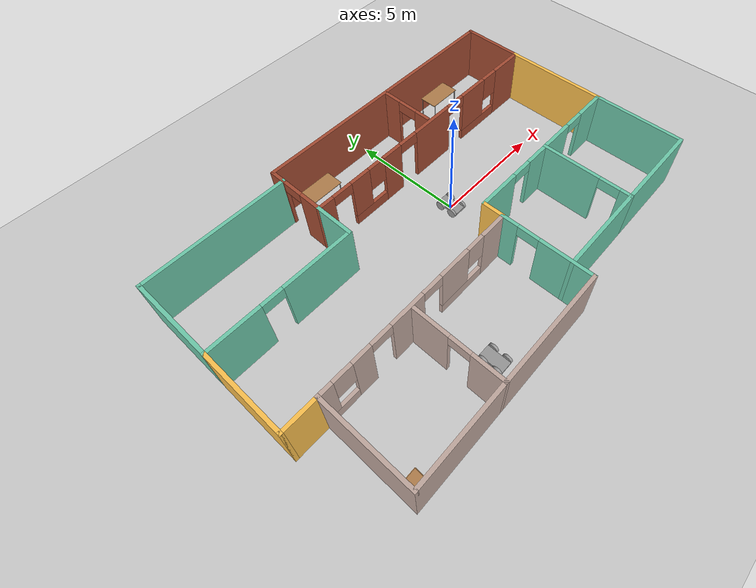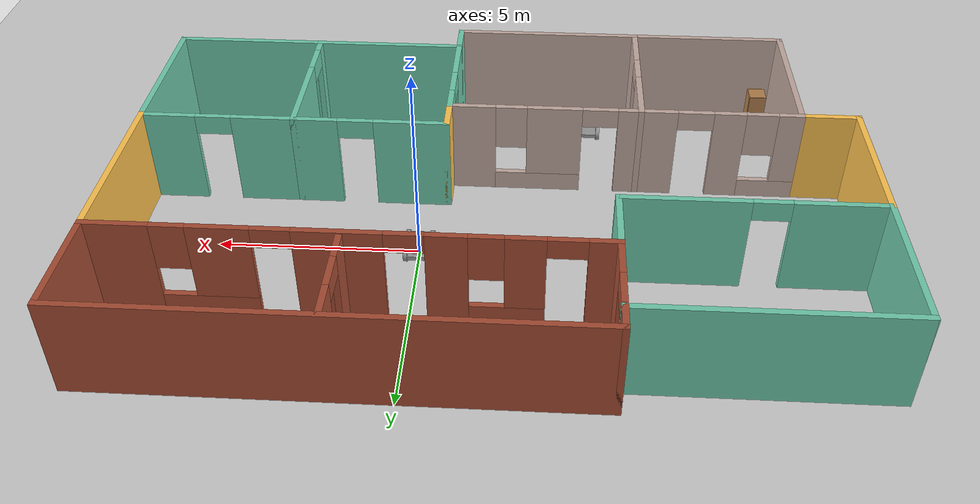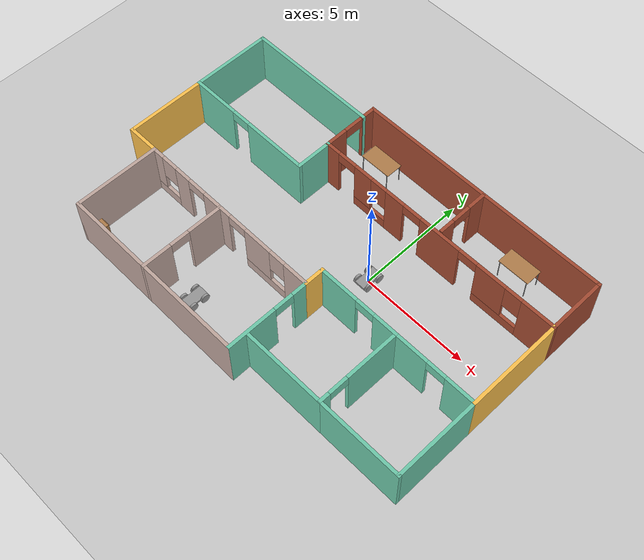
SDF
<sdf version="1.6">
 <world name="default">
  <plugin name="message" filename="libmessage.so"/>
  <light name="sun" type="directional">
   <pose>0 0 10 0 -0 0</pose>
   <diffuse>0.8 0.8 0.8 1</diffuse>
   <specular>0.2 0.2 0.2 1</specular>
   <attenuation>
    <range>1000</range>
    <constant>0.9</constant>
    <linear>0.01</linear>
    <quadratic>0.001</quadratic>
   </attenuation>
   <direction>-0.5 0.1 -0.9</direction>
  </light>
  <model name="ground_plane">
   <static>1</static>
   <link name="link">
    <collision name="collision">
     <geometry><plane><normal>0 0 1</normal><size>100 100</size></plane></geometry>
     <surface><friction><ode><mu>100</mu><mu2>50</mu2></ode></friction></surface>
    </collision>
    <visual name="visual">
     <cast_shadows>0</cast_shadows>
     <geometry><plane><normal>0 0 1</normal><size>100 100</size></plane></geometry>
     <material>
      <script><uri>file://media/materials/scripts/gazebo.material</uri><name>Gazebo/Grey</name></script>
     </material>
    </visual>
   </link>
  </model>
  <gravity>0 0 -9.8</gravity>
  <magnetic_field>6e-06 2.3e-05 -4.2e-05</magnetic_field>
  <atmosphere type="adiabatic"/>
  <physics name="default_physics" default="0" type="ode">
   <max_step_size>0.001</max_step_size>
   <real_time_factor>1</real_time_factor>
   <real_time_update_rate>1000</real_time_update_rate>
  </physics>
  <scene><ambient>0.4 0.4 0.4 1</ambient><background>0.7 0.7 0.7 1</background><shadows>1</shadows></scene>
  <spherical_coordinates>
   <surface_model>EARTH_WGS84</surface_model>
   <latitude_deg>0</latitude_deg>
   <longitude_deg>0</longitude_deg>
   <elevation>0</elevation>
   <heading_deg>0</heading_deg>
  </spherical_coordinates>
  <model name="robot_model">
   <link name="link_0">
    <pose>-0 -2e-06 0 0 -0 0</pose>
    <inertial>
     <mass>1</mass>
     <inertia>
      <ixx>0.166667</ixx>
      <ixy>0</ixy>
      <ixz>0</ixz>
      <iyy>0.166667</iyy>
      <iyz>0</iyz>
      <izz>0.166667</izz>
     </inertia>
    </inertial>
    <visual name="visual">
     <geometry><box><size>0.5 1 0.1</size></box></geometry>
     <material>
      <lighting>1</lighting>
      <script><uri>file://media/materials/scripts/gazebo.material</uri><name>Gazebo/Grey</name></script>
      <ambient>0.3 0.3 0.3 1</ambient>
      <diffuse>0.7 0.7 0.7 1</diffuse>
      <specular>0.01 0.01 0.01 1</specular>
      <emissive>0 0 0 1</emissive>
      <shader type="vertex"><normal_map>__default__</normal_map></shader>
     </material>
    </visual>
    <collision name="collision">
     <geometry><box><size>0.5 1 0.1</size></box></geometry>
     <surface>
      <friction>
       <ode><mu>1</mu><mu2>1</mu2><fdir1>0 0 0</fdir1><slip1>0</slip1><slip2>0</slip2></ode>
       <torsional>
        <coefficient>1</coefficient>
        <patch_radius>0</patch_radius>
        <surface_radius>0</surface_radius>
        <use_patch_radius>1</use_patch_radius>
        <ode><slip>0</slip></ode>
       </torsional>
      </friction>
      <bounce><restitution_coefficient>0</restitution_coefficient><threshold>1e+06</threshold></bounce>
      <contact>
       <collide_without_contact>0</collide_without_contact>
       <collide_without_contact_bitmask>1</collide_without_contact_bitmask>
       <collide_bitmask>1</collide_bitmask>
       <ode>
        <soft_cfm>0</soft_cfm>
        <soft_erp>0.2</soft_erp>
        <kp>1e+13</kp>
        <kd>1</kd>
        <max_vel>0.01</max_vel>
        <min_depth>0</min_depth>
       </ode>
       <bullet>
        <split_impulse>1</split_impulse>
        <split_impulse_penetration_threshold>-0.01</split_impulse_penetration_threshold>
        <soft_cfm>0</soft_cfm>
        <soft_erp>0.2</soft_erp>
        <kp>1e+13</kp>
        <kd>1</kd>
       </bullet>
      </contact>
     </surface>
    </collision>
   </link>
   <link name="link_1">
    <pose>0.300039 -0.299989 0 1.5707 0 1.5707</pose>
    <inertial>
     <mass>1</mass>
     <inertia><ixx>0.145833</ixx><ixy>0</ixy><ixz>0</ixz><iyy>0.145833</iyy><iyz>0</iyz><izz>0.125</izz></inertia>
     <pose>0 0 0.2 0 -0 0</pose>
    </inertial>
    <visual name="visual">
     <geometry><cylinder><radius>0.2</radius><length>0.1</length></cylinder></geometry>
     <material>
      <lighting>1</lighting>
      <script><uri>file://media/materials/scripts/gazebo.material</uri><name>Gazebo/Grey</name></script>
      <ambient>0.3 0.3 0.3 1</ambient>
      <diffuse>0.7 0.7 0.7 1</diffuse>
      <specular>0.01 0.01 0.01 1</specular>
      <emissive>0 0 0 1</emissive>
      <shader type="vertex"><normal_map>__default__</normal_map></shader>
     </material>
    </visual>
    <collision name="collision">
     <geometry><cylinder><radius>0.2</radius><length>0.1</length></cylinder></geometry>
     <surface>
      <friction>
       <ode><mu>1</mu><mu2>1</mu2><fdir1>0 0 0</fdir1><slip1>0</slip1><slip2>0</slip2></ode>
       <torsional>
        <coefficient>1</coefficient>
        <patch_radius>0</patch_radius>
        <surface_radius>0</surface_radius>
        <use_patch_radius>1</use_patch_radius>
        <ode><slip>0</slip></ode>
       </torsional>
      </friction>
      <bounce><restitution_coefficient>0</restitution_coefficient><threshold>1e+06</threshold></bounce>
      <contact>
       <collide_without_contact>0</collide_without_contact>
       <collide_without_contact_bitmask>1</collide_without_contact_bitmask>
       <collide_bitmask>1</collide_bitmask>
       <ode>
        <soft_cfm>0</soft_cfm>
        <soft_erp>0.2</soft_erp>
        <kp>1e+13</kp>
        <kd>1</kd>
        <max_vel>0.01</max_vel>
        <min_depth>0</min_depth>
       </ode>
       <bullet>
        <split_impulse>1</split_impulse>
        <split_impulse_penetration_threshold>-0.01</split_impulse_penetration_threshold>
        <soft_cfm>0</soft_cfm>
        <soft_erp>0.2</soft_erp>
        <kp>1e+13</kp>
        <kd>1</kd>
       </bullet>
      </contact>
     </surface>
    </collision>
   </link>
   <link name="link_1_clone">
    <pose>0.300039 0.299993 0 1.5707 0 1.5707</pose>
    <inertial>
     <mass>1</mass>
     <inertia><ixx>0.145833</ixx><ixy>0</ixy><ixz>0</ixz><iyy>0.145833</iyy><iyz>0</iyz><izz>0.125</izz></inertia>
     <pose>0 0 0.2 0 -0 0</pose>
    </inertial>
    <visual name="visual">
     <geometry><cylinder><radius>0.2</radius><length>0.1</length></cylinder></geometry>
     <material>
      <lighting>1</lighting>
      <script><uri>file://media/materials/scripts/gazebo.material</uri><name>Gazebo/Grey</name></script>
      <ambient>0.3 0.3 0.3 1</ambient>
      <diffuse>0.7 0.7 0.7 1</diffuse>
      <specular>0.01 0.01 0.01 1</specular>
      <emissive>0 0 0 1</emissive>
      <shader type="vertex"><normal_map>__default__</normal_map></shader>
     </material>
    </visual>
    <collision name="collision">
     <geometry><cylinder><radius>0.2</radius><length>0.1</length></cylinder></geometry>
     <surface>
      <friction>
       <ode><mu>1</mu><mu2>1</mu2><fdir1>0 0 0</fdir1><slip1>0</slip1><slip2>0</slip2></ode>
       <torsional>
        <coefficient>1</coefficient>
        <patch_radius>0</patch_radius>
        <surface_radius>0</surface_radius>
        <use_patch_radius>1</use_patch_radius>
        <ode><slip>0</slip></ode>
       </torsional>
      </friction>
      <bounce><restitution_coefficient>0</restitution_coefficient><threshold>1e+06</threshold></bounce>
      <contact>
       <collide_without_contact>0</collide_without_contact>
       <collide_without_contact_bitmask>1</collide_without_contact_bitmask>
       <collide_bitmask>1</collide_bitmask>
       <ode>
        <soft_cfm>0</soft_cfm>
        <soft_erp>0.2</soft_erp>
        <kp>1e+13</kp>
        <kd>1</kd>
        <max_vel>0.01</max_vel>
        <min_depth>0</min_depth>
       </ode>
       <bullet>
        <split_impulse>1</split_impulse>
        <split_impulse_penetration_threshold>-0.01</split_impulse_penetration_threshold>
        <soft_cfm>0</soft_cfm>
        <soft_erp>0.2</soft_erp>
        <kp>1e+13</kp>
        <kd>1</kd>
       </bullet>
      </contact>
     </surface>
    </collision>
   </link>
   <link name="link_1_clone_0">
    <pose>-0.300039 0.299994 0 1.5707 0 1.5707</pose>
    <inertial>
     <mass>1</mass>
     <inertia><ixx>0.145833</ixx><ixy>0</ixy><ixz>0</ixz><iyy>0.145833</iyy><iyz>0</iyz><izz>0.125</izz></inertia>
     <pose>0 0 0.2 0 -0 0</pose>
    </inertial>
    <visual name="visual">
     <geometry><cylinder><radius>0.2</radius><length>0.1</length></cylinder></geometry>
     <material>
      <lighting>1</lighting>
      <script><uri>file://media/materials/scripts/gazebo.material</uri><name>Gazebo/Grey</name></script>
      <ambient>0.3 0.3 0.3 1</ambient>
      <diffuse>0.7 0.7 0.7 1</diffuse>
      <specular>0.01 0.01 0.01 1</specular>
      <emissive>0 0 0 1</emissive>
      <shader type="vertex"><normal_map>__default__</normal_map></shader>
     </material>
    </visual>
    <collision name="collision">
     <geometry><cylinder><radius>0.2</radius><length>0.1</length></cylinder></geometry>
     <surface>
      <friction>
       <ode><mu>1</mu><mu2>1</mu2><fdir1>0 0 0</fdir1><slip1>0</slip1><slip2>0</slip2></ode>
       <torsional>
        <coefficient>1</coefficient>
        <patch_radius>0</patch_radius>
        <surface_radius>0</surface_radius>
        <use_patch_radius>1</use_patch_radius>
        <ode><slip>0</slip></ode>
       </torsional>
      </friction>
      <bounce><restitution_coefficient>0</restitution_coefficient><threshold>1e+06</threshold></bounce>
      <contact>
       <collide_without_contact>0</collide_without_contact>
       <collide_without_contact_bitmask>1</collide_without_contact_bitmask>
       <collide_bitmask>1</collide_bitmask>
       <ode>
        <soft_cfm>0</soft_cfm>
        <soft_erp>0.2</soft_erp>
        <kp>1e+13</kp>
        <kd>1</kd>
        <max_vel>0.01</max_vel>
        <min_depth>0</min_depth>
       </ode>
       <bullet>
        <split_impulse>1</split_impulse>
        <split_impulse_penetration_threshold>-0.01</split_impulse_penetration_threshold>
        <soft_cfm>0</soft_cfm>
        <soft_erp>0.2</soft_erp>
        <kp>1e+13</kp>
        <kd>1</kd>
       </bullet>
      </contact>
     </surface>
    </collision>
   </link>
   <link name="link_1_clone_1">
    <pose>-0.300039 -0.299997 0 1.5707 0 1.5707</pose>
    <inertial>
     <mass>1</mass>
     <inertia><ixx>0.145833</ixx><ixy>0</ixy><ixz>0</ixz><iyy>0.145833</iyy><iyz>0</iyz><izz>0.125</izz></inertia>
     <pose>0 0 0.2 0 -0 0</pose>
    </inertial>
    <visual name="visual">
     <geometry><cylinder><radius>0.2</radius><length>0.1</length></cylinder></geometry>
     <material>
      <lighting>1</lighting>
      <script><uri>file://media/materials/scripts/gazebo.material</uri><name>Gazebo/Grey</name></script>
      <ambient>0.3 0.3 0.3 1</ambient>
      <diffuse>0.7 0.7 0.7 1</diffuse>
      <specular>0.01 0.01 0.01 1</specular>
      <emissive>0 0 0 1</emissive>
      <shader type="vertex"><normal_map>__default__</normal_map></shader>
     </material>
    </visual>
    <collision name="collision">
     <geometry><cylinder><radius>0.2</radius><length>0.1</length></cylinder></geometry>
     <surface>
      <friction>
       <ode><mu>1</mu><mu2>1</mu2><fdir1>0 0 0</fdir1><slip1>0</slip1><slip2>0</slip2></ode>
       <torsional>
        <coefficient>1</coefficient>
        <patch_radius>0</patch_radius>
        <surface_radius>0</surface_radius>
        <use_patch_radius>1</use_patch_radius>
        <ode><slip>0</slip></ode>
       </torsional>
      </friction>
      <bounce><restitution_coefficient>0</restitution_coefficient><threshold>1e+06</threshold></bounce>
      <contact>
       <collide_without_contact>0</collide_without_contact>
       <collide_without_contact_bitmask>1</collide_without_contact_bitmask>
       <collide_bitmask>1</collide_bitmask>
       <ode>
        <soft_cfm>0</soft_cfm>
        <soft_erp>0.2</soft_erp>
        <kp>1e+13</kp>
        <kd>1</kd>
        <max_vel>0.01</max_vel>
        <min_depth>0</min_depth>
       </ode>
       <bullet>
        <split_impulse>1</split_impulse>
        <split_impulse_penetration_threshold>-0.01</split_impulse_penetration_threshold>
        <soft_cfm>0</soft_cfm>
        <soft_erp>0.2</soft_erp>
        <kp>1e+13</kp>
        <kd>1</kd>
       </bullet>
      </contact>
     </surface>
    </collision>
   </link>
   <joint name="link_0_JOINT_0" type="revolute">
    <parent>link_0</parent>
    <child>link_1</child>
    <axis>
     <xyz>0 0 1</xyz>
     <use_parent_model_frame>0</use_parent_model_frame>
     <limit>
      <lower>-1.79769e+308</lower>
      <upper>1.79769e+308</upper>
      <effort>-1</effort>
      <velocity>-1</velocity>
     </limit>
     <dynamics>
      <spring_reference>0</spring_reference>
      <spring_stiffness>0</spring_stiffness>
      <damping>0</damping>
      <friction>0</friction>
     </dynamics>
    </axis>
    <physics>
     <ode><limit><cfm>0</cfm><erp>0.2</erp></limit><suspension><cfm>0</cfm><erp>0.2</erp></suspension></ode>
    </physics>
   </joint>
   <joint name="link_0_JOINT_1" type="revolute">
    <parent>link_0</parent>
    <child>link_1_clone</child>
    <axis>
     <xyz>0 0 1</xyz>
     <use_parent_model_frame>0</use_parent_model_frame>
     <limit>
      <lower>-1.79769e+308</lower>
      <upper>1.79769e+308</upper>
      <effort>-1</effort>
      <velocity>-1</velocity>
     </limit>
     <dynamics>
      <spring_reference>0</spring_reference>
      <spring_stiffness>0</spring_stiffness>
      <damping>0</damping>
     </dynamics>
    </axis>
    <physics>
     <ode><limit><cfm>0</cfm><erp>0.2</erp></limit><suspension><cfm>0</cfm><erp>0.2</erp></suspension></ode>
    </physics>
   </joint>
   <joint name="link_0_JOINT_2" type="revolute">
    <parent>link_0</parent>
    <child>link_1_clone_0</child>
    <axis>
     <xyz>0 0 1</xyz>
     <use_parent_model_frame>0</use_parent_model_frame>
     <limit>
      <lower>-1.79769e+308</lower>
      <upper>1.79769e+308</upper>
      <effort>-1</effort>
      <velocity>-1</velocity>
     </limit>
     <dynamics>
      <spring_reference>0</spring_reference>
      <spring_stiffness>0</spring_stiffness>
      <damping>0</damping>
     </dynamics>
    </axis>
    <physics>
     <ode><limit><cfm>0</cfm><erp>0.2</erp></limit><suspension><cfm>0</cfm><erp>0.2</erp></suspension></ode>
    </physics>
   </joint>
   <joint name="link_1_clone_1_JOINT_3" type="revolute">
    <parent>link_0</parent>
    <child>link_1_clone_1</child>
    <axis>
     <xyz>0 0 1</xyz>
     <use_parent_model_frame>0</use_parent_model_frame>
     <limit>
      <lower>-1.79769e+308</lower>
      <upper>1.79769e+308</upper>
      <effort>-1</effort>
      <velocity>-1</velocity>
     </limit>
     <dynamics>
      <spring_reference>0</spring_reference>
      <spring_stiffness>0</spring_stiffness>
      <damping>0</damping>
     </dynamics>
    </axis>
    <physics>
     <ode><limit><cfm>0</cfm><erp>0.2</erp></limit><suspension><cfm>0</cfm><erp>0.2</erp></suspension></ode>
    </physics>
   </joint>
   <static>0</static>
   <pose>0.002603 -0.000175 0.200003 7e-06 0 -0.003176</pose>
  </model>
  <model name="model_0">
   <pose>-1.81997 -0.881957 0 0 -0 0</pose>
   <link name="Wall_13">
    <pose>-3.575 -3.9 0 0 0 -1.5708</pose>
    <visual name="Wall_13_Visual_0">
     <pose>-1.14969 0 1.25 0 -0 0</pose>
     <geometry><box><size>1.70063 0.15 2.5</size></box></geometry>
     <material>
      <script><uri>file://media/materials/scripts/gazebo.material</uri><name>Gazebo/Grey</name></script>
      <ambient>0.760784 0.662745 0.627451 1</ambient>
     </material>
     <meta><layer>0</layer></meta>
    </visual>
    <collision name="Wall_13_Collision_0">
     <geometry><box><size>1.70063 0.15 2.5</size></box></geometry>
     <pose>-1.14969 0 1.25 0 -0 0</pose>
    </collision>
    <visual name="Wall_13_Visual_1">
     <pose>1.30032 0 1.25 0 -0 0</pose>
     <geometry><box><size>1.39937 0.15 2.5</size></box></geometry>
     <material>
      <script><uri>file://media/materials/scripts/gazebo.material</uri><name>Gazebo/Grey</name></script>
      <ambient>0.760784 0.662745 0.627451 1</ambient>
     </material>
     <meta><layer>0</layer></meta>
    </visual>
    <collision name="Wall_13_Collision_1">
     <geometry><box><size>1.39937 0.15 2.5</size></box></geometry>
     <pose>1.30032 0 1.25 0 -0 0</pose>
    </collision>
    <visual name="Wall_13_Visual_2">
     <pose>0.15063 0 2.25 0 -0 0</pose>
     <geometry><box><size>0.9 0.15 0.5</size></box></geometry>
     <material>
      <script><uri>file://media/materials/scripts/gazebo.material</uri><name>Gazebo/Grey</name></script>
      <ambient>0.760784 0.662745 0.627451 1</ambient>
     </material>
     <meta><layer>0</layer></meta>
    </visual>
    <collision name="Wall_13_Collision_2">
     <geometry><box><size>0.9 0.15 0.5</size></box></geometry>
     <pose>0.15063 0 2.25 0 -0 0</pose>
    </collision>
   </link>
   <link name="Wall_14">
    <collision name="Wall_14_Collision">
     <geometry><box><size>5 0.15 2.5</size></box></geometry>
     <pose>0 0 1.25 0 -0 0</pose>
    </collision>
    <visual name="Wall_14_Visual">
     <pose>0 0 1.25 0 -0 0</pose>
     <geometry><box><size>5 0.15 2.5</size></box></geometry>
     <material>
      <script><uri>file://media/materials/scripts/gazebo.material</uri><name>Gazebo/Grey</name></script>
      <ambient>0.760784 0.662745 0.627451 1</ambient>
     </material>
     <meta><layer>0</layer></meta>
    </visual>
    <pose>-1.15 -5.825 0 0 -0 0</pose>
   </link>
   <link name="Wall_15">
    <pose>1.275 -3.9 0 0 -0 1.5708</pose>
    <visual name="Wall_15_Visual_0">
     <pose>-0.837703 0 1.25 0 -0 0</pose>
     <geometry><box><size>2.32459 0.15 2.5</size></box></geometry>
     <material>
      <script><uri>file://media/materials/scripts/gazebo.material</uri><name>Gazebo/Grey</name></script>
      <ambient>0.435294 0.796078 0.67451 1</ambient>
     </material>
     <meta><layer>0</layer></meta>
    </visual>
    <collision name="Wall_15_Collision_0">
     <geometry><box><size>2.32459 0.15 2.5</size></box></geometry>
     <pose>-0.837703 0 1.25 0 -0 0</pose>
    </collision>
    <visual name="Wall_15_Visual_1">
     <pose>1.6123 0 1.25 0 -0 0</pose>
     <geometry><box><size>0.775406 0.15 2.5</size></box></geometry>
     <material>
      <script><uri>file://media/materials/scripts/gazebo.material</uri><name>Gazebo/Grey</name></script>
      <ambient>0.435294 0.796078 0.67451 1</ambient>
     </material>
     <meta><layer>0</layer></meta>
    </visual>
    <collision name="Wall_15_Collision_1">
     <geometry><box><size>0.775406 0.15 2.5</size></box></geometry>
     <pose>1.6123 0 1.25 0 -0 0</pose>
    </collision>
    <visual name="Wall_15_Visual_2">
     <pose>0.774594 0 2.25 0 -0 0</pose>
     <geometry><box><size>0.9 0.15 0.5</size></box></geometry>
     <material>
      <script><uri>file://media/materials/scripts/gazebo.material</uri><name>Gazebo/Grey</name></script>
      <ambient>0.435294 0.796078 0.67451 1</ambient>
     </material>
     <meta><layer>0</layer></meta>
    </visual>
    <collision name="Wall_15_Collision_2">
     <geometry><box><size>0.9 0.15 0.5</size></box></geometry>
     <pose>0.774594 0 2.25 0 -0 0</pose>
    </collision>
   </link>
   <link name="Wall_16">
    <pose>-3.15 -1.975 0 0 -0 3.14159</pose>
    <visual name="Wall_16_Visual_0">
     <pose>-3.87671 0 1.25 0 -0 0</pose>
     <geometry><box><size>1.24658 0.15 2.5</size></box></geometry>
     <material>
      <script><uri>file://media/materials/scripts/gazebo.material</uri><name>Gazebo/Grey</name></script>
      <ambient>0.760784 0.662745 0.627451 1</ambient>
     </material>
     <meta><layer>0</layer></meta>
    </visual>
    <collision name="Wall_16_Collision_0">
     <geometry><box><size>1.24658 0.15 2.5</size></box></geometry>
     <pose>-3.87671 0 1.25 0 -0 0</pose>
    </collision>
    <visual name="Wall_16_Visual_1">
     <pose>0.598963 0 1.25 0 -0 0</pose>
     <geometry><box><size>1.50298 0.15 2.5</size></box></geometry>
     <material>
      <script><uri>file://media/materials/scripts/gazebo.material</uri><name>Gazebo/Grey</name></script>
      <ambient>0.760784 0.662745 0.627451 1</ambient>
     </material>
     <meta><layer>0</layer></meta>
    </visual>
    <collision name="Wall_16_Collision_1">
     <geometry><box><size>1.50298 0.15 2.5</size></box></geometry>
     <pose>0.598963 0 1.25 0 -0 0</pose>
    </collision>
    <visual name="Wall_16_Visual_2">
     <pose>2.65433 0 1.25 0 -0 0</pose>
     <geometry><box><size>0.807753 0.15 2.5</size></box></geometry>
     <material>
      <script><uri>file://media/materials/scripts/gazebo.material</uri><name>Gazebo/Grey</name></script>
      <ambient>0.760784 0.662745 0.627451 1</ambient>
     </material>
     <meta><layer>0</layer></meta>
    </visual>
    <collision name="Wall_16_Collision_2">
     <geometry><box><size>0.807753 0.15 2.5</size></box></geometry>
     <pose>2.65433 0 1.25 0 -0 0</pose>
    </collision>
    <visual name="Wall_16_Visual_3">
     <pose>-2.15298 0 0.25 0 -0 0</pose>
     <geometry><box><size>2.2009 0.15 0.5</size></box></geometry>
     <material>
      <script><uri>file://media/materials/scripts/gazebo.material</uri><name>Gazebo/Grey</name></script>
      <ambient>0.760784 0.662745 0.627451 1</ambient>
     </material>
     <meta><layer>0</layer></meta>
    </visual>
    <collision name="Wall_16_Collision_3">
     <geometry><box><size>2.2009 0.15 0.5</size></box></geometry>
     <pose>-2.15298 0 0.25 0 -0 0</pose>
    </collision>
    <visual name="Wall_16_Visual_4">
     <pose>3.7791 0 0.25 0 -0 0</pose>
     <geometry><box><size>1.44179 0.15 0.5</size></box></geometry>
     <material>
      <script><uri>file://media/materials/scripts/gazebo.material</uri><name>Gazebo/Grey</name></script>
      <ambient>0.760784 0.662745 0.627451 1</ambient>
     </material>
     <meta><layer>0</layer></meta>
    </visual>
    <collision name="Wall_16_Collision_4">
     <geometry><box><size>1.44179 0.15 0.5</size></box></geometry>
     <pose>3.7791 0 0.25 0 -0 0</pose>
    </collision>
    <visual name="Wall_16_Visual_5">
     <pose>-1.75298 0 1.5 0 -0 0</pose>
     <geometry><box><size>1.4009 0.15 2</size></box></geometry>
     <material>
      <script><uri>file://media/materials/scripts/gazebo.material</uri><name>Gazebo/Grey</name></script>
      <ambient>0.760784 0.662745 0.627451 1</ambient>
     </material>
     <meta><layer>0</layer></meta>
    </visual>
    <collision name="Wall_16_Collision_5">
     <geometry><box><size>1.4009 0.15 2</size></box></geometry>
     <pose>-1.75298 0 1.5 0 -0 0</pose>
    </collision>
    <visual name="Wall_16_Visual_6">
     <pose>-1.75298 0 1.5 0 -0 0</pose>
     <geometry><box><size>1.4009 0.15 2</size></box></geometry>
     <material>
      <script><uri>file://media/materials/scripts/gazebo.material</uri><name>Gazebo/Grey</name></script>
      <ambient>0.760784 0.662745 0.627451 1</ambient>
     </material>
     <meta><layer>0</layer></meta>
    </visual>
    <collision name="Wall_16_Collision_6">
     <geometry><box><size>1.4009 0.15 2</size></box></geometry>
     <pose>-1.75298 0 1.5 0 -0 0</pose>
    </collision>
    <visual name="Wall_16_Visual_7">
     <pose>4.1791 0 1.5 0 -0 0</pose>
     <geometry><box><size>0.641792 0.15 2</size></box></geometry>
     <material>
      <script><uri>file://media/materials/scripts/gazebo.material</uri><name>Gazebo/Grey</name></script>
      <ambient>0.760784 0.662745 0.627451 1</ambient>
     </material>
     <meta><layer>0</layer></meta>
    </visual>
    <collision name="Wall_16_Collision_7">
     <geometry><box><size>0.641792 0.15 2</size></box></geometry>
     <pose>4.1791 0 1.5 0 -0 0</pose>
    </collision>
    <visual name="Wall_16_Visual_8">
     <pose>-2.85342 0 1.9 0 -0 0</pose>
     <geometry><box><size>0.8 0.15 1.2</size></box></geometry>
     <material>
      <script><uri>file://media/materials/scripts/gazebo.material</uri><name>Gazebo/Grey</name></script>
      <ambient>0.760784 0.662745 0.627451 1</ambient>
     </material>
     <meta><layer>0</layer></meta>
    </visual>
    <collision name="Wall_16_Collision_8">
     <geometry><box><size>0.8 0.15 1.2</size></box></geometry>
     <pose>-2.85342 0 1.9 0 -0 0</pose>
    </collision>
    <visual name="Wall_16_Visual_9">
     <pose>3.45821 0 1.9 0 -0 0</pose>
     <geometry><box><size>0.8 0.15 1.2</size></box></geometry>
     <material>
      <script><uri>file://media/materials/scripts/gazebo.material</uri><name>Gazebo/Grey</name></script>
      <ambient>0.760784 0.662745 0.627451 1</ambient>
     </material>
     <meta><layer>0</layer></meta>
    </visual>
    <collision name="Wall_16_Collision_9">
     <geometry><box><size>0.8 0.15 1.2</size></box></geometry>
     <pose>3.45821 0 1.9 0 -0 0</pose>
    </collision>
    <visual name="Wall_16_Visual_10">
     <pose>1.80045 0 2.25 0 -0 0</pose>
     <geometry><box><size>0.9 0.15 0.5</size></box></geometry>
     <material>
      <script><uri>file://media/materials/scripts/gazebo.material</uri><name>Gazebo/Grey</name></script>
      <ambient>0.760784 0.662745 0.627451 1</ambient>
     </material>
     <meta><layer>0</layer></meta>
    </visual>
    <collision name="Wall_16_Collision_10">
     <geometry><box><size>0.9 0.15 0.5</size></box></geometry>
     <pose>1.80045 0 2.25 0 -0 0</pose>
    </collision>
    <visual name="Wall_16_Visual_11">
     <pose>-0.602528 0 2.25 0 -0 0</pose>
     <geometry><box><size>0.9 0.15 0.5</size></box></geometry>
     <material>
      <script><uri>file://media/materials/scripts/gazebo.material</uri><name>Gazebo/Grey</name></script>
      <ambient>0.760784 0.662745 0.627451 1</ambient>
     </material>
     <meta><layer>0</layer></meta>
    </visual>
    <collision name="Wall_16_Collision_11">
     <geometry><box><size>0.9 0.15 0.5</size></box></geometry>
     <pose>-0.602528 0 2.25 0 -0 0</pose>
    </collision>
    <visual name="Wall_16_Visual_12">
     <pose>-0.602528 0 2.25 0 -0 0</pose>
     <geometry><box><size>0.9 0.15 0.5</size></box></geometry>
     <material>
      <script><uri>file://media/materials/scripts/gazebo.material</uri><name>Gazebo/Grey</name></script>
      <ambient>0.760784 0.662745 0.627451 1</ambient>
     </material>
     <meta><layer>0</layer></meta>
    </visual>
    <collision name="Wall_16_Collision_12">
     <geometry><box><size>0.9 0.15 0.5</size></box></geometry>
     <pose>-0.602528 0 2.25 0 -0 0</pose>
    </collision>
   </link>
   <link name="Wall_17">
    <collision name="Wall_17_Collision">
     <geometry><box><size>4 0.15 2.5</size></box></geometry>
     <pose>0 0 1.25 0 -0 0</pose>
    </collision>
    <visual name="Wall_17_Visual">
     <pose>0 0 1.25 0 -0 0</pose>
     <geometry><box><size>4 0.15 2.5</size></box></geometry>
     <material>
      <script><uri>file://media/materials/scripts/gazebo.material</uri><name>Gazebo/Grey</name></script>
      <ambient>0.760784 0.662745 0.627451 1</ambient>
     </material>
     <meta><layer>0</layer></meta>
    </visual>
    <pose>-7.575 -3.9 0 0 0 -1.5708</pose>
   </link>
   <link name="Wall_18">
    <collision name="Wall_18_Collision">
     <geometry><box><size>4 0.15 2.5</size></box></geometry>
     <pose>0 0 1.25 0 -0 0</pose>
    </collision>
    <visual name="Wall_18_Visual">
     <pose>0 0 1.25 0 -0 0</pose>
     <geometry><box><size>4 0.15 2.5</size></box></geometry>
     <material>
      <script><uri>file://media/materials/scripts/gazebo.material</uri><name>Gazebo/Grey</name></script>
      <ambient>0.760784 0.662745 0.627451 1</ambient>
     </material>
     <meta><layer>0</layer></meta>
    </visual>
    <pose>-5.65 -5.825 0 0 -0 0</pose>
   </link>
   <link name="Wall_27">
    <collision name="Wall_27_Collision">
     <geometry><box><size>1 0.15 2.5</size></box></geometry>
     <pose>0 0 1.25 0 -0 0</pose>
    </collision>
    <visual name="Wall_27_Visual">
     <pose>0 0 1.25 0 -0 0</pose>
     <geometry><box><size>1 0.15 2.5</size></box></geometry>
     <material>
      <script><uri>file://media/materials/scripts/gazebo.material</uri><name>Gazebo/Grey</name></script>
      <ambient>1 0.764706 0.305882 1</ambient>
     </material>
     <meta><layer>0</layer></meta>
    </visual>
    <pose>1.275 -1.55 0 0 -0 1.5708</pose>
   </link>
   <link name="Wall_28">
    <pose>3.2 -1.125 0 0 -0 0</pose>
    <visual name="Wall_28_Visual_0">
     <pose>-1.04345 0 1.25 0 -0 0</pose>
     <geometry><box><size>1.9131 0.15 2.5</size></box></geometry>
     <material>
      <script><uri>file://media/materials/scripts/gazebo.material</uri><name>Gazebo/Grey</name></script>
      <ambient>0.435294 0.796078 0.67451 1</ambient>
     </material>
     <meta><layer>0</layer></meta>
    </visual>
    <collision name="Wall_28_Collision_0">
     <geometry><box><size>1.9131 0.15 2.5</size></box></geometry>
     <pose>-1.04345 0 1.25 0 -0 0</pose>
    </collision>
    <visual name="Wall_28_Visual_1">
     <pose>1.40655 0 1.25 0 -0 0</pose>
     <geometry><box><size>1.1869 0.15 2.5</size></box></geometry>
     <material>
      <script><uri>file://media/materials/scripts/gazebo.material</uri><name>Gazebo/Grey</name></script>
      <ambient>0.435294 0.796078 0.67451 1</ambient>
     </material>
     <meta><layer>0</layer></meta>
    </visual>
    <collision name="Wall_28_Collision_1">
     <geometry><box><size>1.1869 0.15 2.5</size></box></geometry>
     <pose>1.40655 0 1.25 0 -0 0</pose>
    </collision>
    <visual name="Wall_28_Visual_2">
     <pose>0.363098 0 2.25 0 -0 0</pose>
     <geometry><box><size>0.9 0.15 0.5</size></box></geometry>
     <material>
      <script><uri>file://media/materials/scripts/gazebo.material</uri><name>Gazebo/Grey</name></script>
      <ambient>0.435294 0.796078 0.67451 1</ambient>
     </material>
     <meta><layer>0</layer></meta>
    </visual>
    <collision name="Wall_28_Collision_2">
     <geometry><box><size>0.9 0.15 0.5</size></box></geometry>
     <pose>0.363098 0 2.25 0 -0 0</pose>
    </collision>
   </link>
   <link name="Wall_29">
    <pose>5.125 -3.05 0 0 0 -1.5708</pose>
    <visual name="Wall_29_Visual_0">
     <pose>-0.71312 0 1.25 0 -0 0</pose>
     <geometry><box><size>2.57376 0.15 2.5</size></box></geometry>
     <material>
      <script><uri>file://media/materials/scripts/gazebo.material</uri><name>Gazebo/Grey</name></script>
      <ambient>0.435294 0.796078 0.67451 1</ambient>
     </material>
     <meta><layer>0</layer></meta>
    </visual>
    <collision name="Wall_29_Collision_0">
     <geometry><box><size>2.57376 0.15 2.5</size></box></geometry>
     <pose>-0.71312 0 1.25 0 -0 0</pose>
    </collision>
    <visual name="Wall_29_Visual_1">
     <pose>1.73688 0 1.25 0 -0 0</pose>
     <geometry><box><size>0.52624 0.15 2.5</size></box></geometry>
     <material>
      <script><uri>file://media/materials/scripts/gazebo.material</uri><name>Gazebo/Grey</name></script>
      <ambient>0.435294 0.796078 0.67451 1</ambient>
     </material>
     <meta><layer>0</layer></meta>
    </visual>
    <collision name="Wall_29_Collision_1">
     <geometry><box><size>0.52624 0.15 2.5</size></box></geometry>
     <pose>1.73688 0 1.25 0 -0 0</pose>
    </collision>
    <visual name="Wall_29_Visual_2">
     <pose>1.02376 0 2.25 0 -0 0</pose>
     <geometry><box><size>0.9 0.15 0.5</size></box></geometry>
     <material>
      <script><uri>file://media/materials/scripts/gazebo.material</uri><name>Gazebo/Grey</name></script>
      <ambient>0.435294 0.796078 0.67451 1</ambient>
     </material>
     <meta><layer>0</layer></meta>
    </visual>
    <collision name="Wall_29_Collision_2">
     <geometry><box><size>0.9 0.15 0.5</size></box></geometry>
     <pose>1.02376 0 2.25 0 -0 0</pose>
    </collision>
   </link>
   <link name="Wall_30">
    <collision name="Wall_30_Collision">
     <geometry><box><size>4 0.15 2.5</size></box></geometry>
     <pose>0 0 1.25 0 -0 0</pose>
    </collision>
    <visual name="Wall_30_Visual">
     <pose>0 0 1.25 0 -0 0</pose>
     <geometry><box><size>4 0.15 2.5</size></box></geometry>
     <material>
      <script><uri>file://media/materials/scripts/gazebo.material</uri><name>Gazebo/Grey</name></script>
      <ambient>0.435294 0.796078 0.67451 1</ambient>
     </material>
     <meta><layer>0</layer></meta>
    </visual>
    <pose>3.2 -4.975 0 0 -0 3.14159</pose>
   </link>
   <link name="Wall_32">
    <pose>7.05 -1.125 0 0 -0 0</pose>
    <visual name="Wall_32_Visual_0">
     <pose>-1.17583 0 1.25 0 -0 0</pose>
     <geometry><box><size>1.64834 0.15 2.5</size></box></geometry>
     <material>
      <script><uri>file://media/materials/scripts/gazebo.material</uri><name>Gazebo/Grey</name></script>
      <ambient>0.435294 0.796078 0.67451 1</ambient>
     </material>
     <meta><layer>0</layer></meta>
    </visual>
    <collision name="Wall_32_Collision_0">
     <geometry><box><size>1.64834 0.15 2.5</size></box></geometry>
     <pose>-1.17583 0 1.25 0 -0 0</pose>
    </collision>
    <visual name="Wall_32_Visual_1">
     <pose>1.27417 0 1.25 0 -0 0</pose>
     <geometry><box><size>1.45166 0.15 2.5</size></box></geometry>
     <material>
      <script><uri>file://media/materials/scripts/gazebo.material</uri><name>Gazebo/Grey</name></script>
      <ambient>0.435294 0.796078 0.67451 1</ambient>
     </material>
     <meta><layer>0</layer></meta>
    </visual>
    <collision name="Wall_32_Collision_1">
     <geometry><box><size>1.45166 0.15 2.5</size></box></geometry>
     <pose>1.27417 0 1.25 0 -0 0</pose>
    </collision>
    <visual name="Wall_32_Visual_2">
     <pose>0.098342 0 2.25 0 -0 0</pose>
     <geometry><box><size>0.9 0.15 0.5</size></box></geometry>
     <material>
      <script><uri>file://media/materials/scripts/gazebo.material</uri><name>Gazebo/Grey</name></script>
      <ambient>0.435294 0.796078 0.67451 1</ambient>
     </material>
     <meta><layer>0</layer></meta>
    </visual>
    <collision name="Wall_32_Collision_2">
     <geometry><box><size>0.9 0.15 0.5</size></box></geometry>
     <pose>0.098342 0 2.25 0 -0 0</pose>
    </collision>
   </link>
   <link name="Wall_33">
    <collision name="Wall_33_Collision">
     <geometry><box><size>4 0.15 2.5</size></box></geometry>
     <pose>0 0 1.25 0 -0 0</pose>
    </collision>
    <visual name="Wall_33_Visual">
     <pose>0 0 1.25 0 -0 0</pose>
     <geometry><box><size>4 0.15 2.5</size></box></geometry>
     <material>
      <script><uri>file://media/materials/scripts/gazebo.material</uri><name>Gazebo/Grey</name></script>
      <ambient>0.435294 0.796078 0.67451 1</ambient>
     </material>
     <meta><layer>0</layer></meta>
    </visual>
    <pose>8.975 -3.05 0 0 0 -1.5708</pose>
   </link>
   <link name="Wall_34">
    <collision name="Wall_34_Collision">
     <geometry><box><size>4 0.15 2.5</size></box></geometry>
     <pose>0 0 1.25 0 -0 0</pose>
    </collision>
    <visual name="Wall_34_Visual">
     <pose>0 0 1.25 0 -0 0</pose>
     <geometry><box><size>4 0.15 2.5</size></box></geometry>
     <material>
      <script><uri>file://media/materials/scripts/gazebo.material</uri><name>Gazebo/Grey</name></script>
      <ambient>0.435294 0.796078 0.67451 1</ambient>
     </material>
     <meta><layer>0</layer></meta>
    </visual>
    <pose>7.05 -4.975 0 0 -0 3.14159</pose>
   </link>
   <link name="Wall_36">
    <collision name="Wall_36_Collision">
     <geometry><box><size>4.5 0.15 2.5</size></box></geometry>
     <pose>0 0 1.25 0 -0 0</pose>
    </collision>
    <visual name="Wall_36_Visual">
     <pose>0 0 1.25 0 -0 0</pose>
     <geometry><box><size>4.5 0.15 2.5</size></box></geometry>
     <material>
      <script><uri>file://media/materials/scripts/gazebo.material</uri><name>Gazebo/Grey</name></script>
      <ambient>1 0.764706 0.305882 1</ambient>
     </material>
     <meta><layer>0</layer></meta>
    </visual>
    <pose>8.975 1.05 0 0 -0 1.5708</pose>
   </link>
   <link name="Wall_37">
    <pose>3.05 3.225 0 0 -0 3.14159</pose>
    <visual name="Wall_37_Visual_0">
     <pose>-5.19543 0 1.25 0 -0 0</pose>
     <geometry><box><size>1.60914 0.15 2.5</size></box></geometry>
     <material>
      <script><uri>file://media/materials/scripts/gazebo.material</uri><name>Gazebo/Bricks</name></script>
      <ambient>0.996078 0.47451 0.0196078 1</ambient>
     </material>
     <meta><layer>0</layer></meta>
    </visual>
    <collision name="Wall_37_Collision_0">
     <geometry><box><size>1.60914 0.15 2.5</size></box></geometry>
     <pose>-5.19543 0 1.25 0 -0 0</pose>
    </collision>
    <visual name="Wall_37_Visual_1">
     <pose>-0.241571 0 1.25 0 -0 0</pose>
     <geometry><box><size>2.02272 0.15 2.5</size></box></geometry>
     <material>
      <script><uri>file://media/materials/scripts/gazebo.material</uri><name>Gazebo/Bricks</name></script>
      <ambient>0.996078 0.47451 0.0196078 1</ambient>
     </material>
     <meta><layer>0</layer></meta>
    </visual>
    <collision name="Wall_37_Collision_1">
     <geometry><box><size>2.02272 0.15 2.5</size></box></geometry>
     <pose>-0.241571 0 1.25 0 -0 0</pose>
    </collision>
    <visual name="Wall_37_Visual_2">
     <pose>2.14409 0 1.25 0 -0 0</pose>
     <geometry><box><size>0.9486 0.15 2.5</size></box></geometry>
     <material>
      <script><uri>file://media/materials/scripts/gazebo.material</uri><name>Gazebo/Bricks</name></script>
      <ambient>0.996078 0.47451 0.0196078 1</ambient>
     </material>
     <meta><layer>0</layer></meta>
    </visual>
    <collision name="Wall_37_Collision_2">
     <geometry><box><size>0.9486 0.15 2.5</size></box></geometry>
     <pose>2.14409 0 1.25 0 -0 0</pose>
    </collision>
    <visual name="Wall_37_Visual_3">
     <pose>5.62027 0 1.25 0 -0 0</pose>
     <geometry><box><size>0.759458 0.15 2.5</size></box></geometry>
     <material>
      <script><uri>file://media/materials/scripts/gazebo.material</uri><name>Gazebo/Bricks</name></script>
      <ambient>0.996078 0.47451 0.0196078 1</ambient>
     </material>
     <meta><layer>0</layer></meta>
    </visual>
    <collision name="Wall_37_Collision_3">
     <geometry><box><size>0.759458 0.15 2.5</size></box></geometry>
     <pose>5.62027 0 1.25 0 -0 0</pose>
    </collision>
    <visual name="Wall_37_Visual_4">
     <pose>-3.2719 0 0.25 0 -0 0</pose>
     <geometry><box><size>2.23793 0.15 0.5</size></box></geometry>
     <material>
      <script><uri>file://media/materials/scripts/gazebo.material</uri><name>Gazebo/Bricks</name></script>
      <ambient>0.996078 0.47451 0.0196078 1</ambient>
     </material>
     <meta><layer>0</layer></meta>
    </visual>
    <collision name="Wall_37_Collision_4">
     <geometry><box><size>2.23793 0.15 0.5</size></box></geometry>
     <pose>-3.2719 0 0.25 0 -0 0</pose>
    </collision>
    <visual name="Wall_37_Visual_5">
     <pose>3.47947 0 0.25 0 -0 0</pose>
     <geometry><box><size>1.72215 0.15 0.5</size></box></geometry>
     <material>
      <script><uri>file://media/materials/scripts/gazebo.material</uri><name>Gazebo/Bricks</name></script>
      <ambient>0.996078 0.47451 0.0196078 1</ambient>
     </material>
     <meta><layer>0</layer></meta>
    </visual>
    <collision name="Wall_37_Collision_5">
     <geometry><box><size>1.72215 0.15 0.5</size></box></geometry>
     <pose>3.47947 0 0.25 0 -0 0</pose>
    </collision>
    <visual name="Wall_37_Visual_6">
     <pose>-2.8719 0 1.5 0 -0 0</pose>
     <geometry><box><size>1.43792 0.15 2</size></box></geometry>
     <material>
      <script><uri>file://media/materials/scripts/gazebo.material</uri><name>Gazebo/Bricks</name></script>
      <ambient>0.996078 0.47451 0.0196078 1</ambient>
     </material>
     <meta><layer>0</layer></meta>
    </visual>
    <collision name="Wall_37_Collision_6">
     <geometry><box><size>1.43792 0.15 2</size></box></geometry>
     <pose>-2.8719 0 1.5 0 -0 0</pose>
    </collision>
    <visual name="Wall_37_Visual_7">
     <pose>-2.8719 0 1.5 0 -0 0</pose>
     <geometry><box><size>1.43792 0.15 2</size></box></geometry>
     <material>
      <script><uri>file://media/materials/scripts/gazebo.material</uri><name>Gazebo/Bricks</name></script>
      <ambient>0.996078 0.47451 0.0196078 1</ambient>
     </material>
     <meta><layer>0</layer></meta>
    </visual>
    <collision name="Wall_37_Collision_7">
     <geometry><box><size>1.43792 0.15 2</size></box></geometry>
     <pose>-2.8719 0 1.5 0 -0 0</pose>
    </collision>
    <visual name="Wall_37_Visual_8">
     <pose>3.87947 0 1.5 0 -0 0</pose>
     <geometry><box><size>0.92215 0.15 2</size></box></geometry>
     <material>
      <script><uri>file://media/materials/scripts/gazebo.material</uri><name>Gazebo/Bricks</name></script>
      <ambient>0.996078 0.47451 0.0196078 1</ambient>
     </material>
     <meta><layer>0</layer></meta>
    </visual>
    <collision name="Wall_37_Collision_8">
     <geometry><box><size>0.92215 0.15 2</size></box></geometry>
     <pose>3.87947 0 1.5 0 -0 0</pose>
    </collision>
    <visual name="Wall_37_Visual_9">
     <pose>-3.99086 0 1.9 0 -0 0</pose>
     <geometry><box><size>0.8 0.15 1.2</size></box></geometry>
     <material>
      <script><uri>file://media/materials/scripts/gazebo.material</uri><name>Gazebo/Bricks</name></script>
      <ambient>0.996078 0.47451 0.0196078 1</ambient>
     </material>
     <meta><layer>0</layer></meta>
    </visual>
    <collision name="Wall_37_Collision_9">
     <geometry><box><size>0.8 0.15 1.2</size></box></geometry>
     <pose>-3.99086 0 1.9 0 -0 0</pose>
    </collision>
    <visual name="Wall_37_Visual_10">
     <pose>3.01839 0 1.9 0 -0 0</pose>
     <geometry><box><size>0.8 0.15 1.2</size></box></geometry>
     <material>
      <script><uri>file://media/materials/scripts/gazebo.material</uri><name>Gazebo/Bricks</name></script>
      <ambient>0.996078 0.47451 0.0196078 1</ambient>
     </material>
     <meta><layer>0</layer></meta>
    </visual>
    <collision name="Wall_37_Collision_10">
     <geometry><box><size>0.8 0.15 1.2</size></box></geometry>
     <pose>3.01839 0 1.9 0 -0 0</pose>
    </collision>
    <visual name="Wall_37_Visual_11">
     <pose>1.21979 0 2.25 0 -0 0</pose>
     <geometry><box><size>0.9 0.15 0.5</size></box></geometry>
     <material>
      <script><uri>file://media/materials/scripts/gazebo.material</uri><name>Gazebo/Bricks</name></script>
      <ambient>0.996078 0.47451 0.0196078 1</ambient>
     </material>
     <meta><layer>0</layer></meta>
    </visual>
    <collision name="Wall_37_Collision_11">
     <geometry><box><size>0.9 0.15 0.5</size></box></geometry>
     <pose>1.21979 0 2.25 0 -0 0</pose>
    </collision>
    <visual name="Wall_37_Visual_12">
     <pose>-1.70293 0 2.25 0 -0 0</pose>
     <geometry><box><size>0.9 0.15 0.5</size></box></geometry>
     <material>
      <script><uri>file://media/materials/scripts/gazebo.material</uri><name>Gazebo/Bricks</name></script>
      <ambient>0.996078 0.47451 0.0196078 1</ambient>
     </material>
     <meta><layer>0</layer></meta>
    </visual>
    <collision name="Wall_37_Collision_12">
     <geometry><box><size>0.9 0.15 0.5</size></box></geometry>
     <pose>-1.70293 0 2.25 0 -0 0</pose>
    </collision>
    <visual name="Wall_37_Visual_13">
     <pose>-1.70293 0 2.25 0 -0 0</pose>
     <geometry><box><size>0.9 0.15 0.5</size></box></geometry>
     <material>
      <script><uri>file://media/materials/scripts/gazebo.material</uri><name>Gazebo/Bricks</name></script>
      <ambient>0.996078 0.47451 0.0196078 1</ambient>
     </material>
     <meta><layer>0</layer></meta>
    </visual>
    <collision name="Wall_37_Collision_13">
     <geometry><box><size>0.9 0.15 0.5</size></box></geometry>
     <pose>-1.70293 0 2.25 0 -0 0</pose>
    </collision>
    <visual name="Wall_37_Visual_14">
     <pose>4.79054 0 2.25 0 -0 0</pose>
     <geometry><box><size>0.9 0.15 0.5</size></box></geometry>
     <material>
      <script><uri>file://media/materials/scripts/gazebo.material</uri><name>Gazebo/Bricks</name></script>
      <ambient>0.996078 0.47451 0.0196078 1</ambient>
     </material>
     <meta><layer>0</layer></meta>
    </visual>
    <collision name="Wall_37_Collision_14">
     <geometry><box><size>0.9 0.15 0.5</size></box></geometry>
     <pose>4.79054 0 2.25 0 -0 0</pose>
    </collision>
   </link>
   <link name="Wall_38">
    <pose>-2.875 4.525 0 0 -0 1.5708</pose>
    <visual name="Wall_38_Visual_0">
     <pose>-0.840195 0 1.25 0 -0 0</pose>
     <geometry><box><size>1.06961 0.15 2.5</size></box></geometry>
     <material>
      <script><uri>file://media/materials/scripts/gazebo.material</uri><name>Gazebo/Bricks</name></script>
      <ambient>0.996078 0.47451 0.0196078 1</ambient>
     </material>
     <meta><layer>0</layer></meta>
    </visual>
    <collision name="Wall_38_Collision_0">
     <geometry><box><size>1.06961 0.15 2.5</size></box></geometry>
     <pose>-0.840195 0 1.25 0 -0 0</pose>
    </collision>
    <visual name="Wall_38_Visual_1">
     <pose>0.984805 0 1.25 0 -0 0</pose>
     <geometry><box><size>0.780391 0.15 2.5</size></box></geometry>
     <material>
      <script><uri>file://media/materials/scripts/gazebo.material</uri><name>Gazebo/Bricks</name></script>
      <ambient>0.996078 0.47451 0.0196078 1</ambient>
     </material>
     <meta><layer>0</layer></meta>
    </visual>
    <collision name="Wall_38_Collision_1">
     <geometry><box><size>0.780391 0.15 2.5</size></box></geometry>
     <pose>0.984805 0 1.25 0 -0 0</pose>
    </collision>
    <visual name="Wall_38_Visual_2">
     <pose>0.144609 0 2.25 0 -0 0</pose>
     <geometry><box><size>0.9 0.15 0.5</size></box></geometry>
     <material>
      <script><uri>file://media/materials/scripts/gazebo.material</uri><name>Gazebo/Bricks</name></script>
      <ambient>0.996078 0.47451 0.0196078 1</ambient>
     </material>
     <meta><layer>0</layer></meta>
    </visual>
    <collision name="Wall_38_Collision_2">
     <geometry><box><size>0.9 0.15 0.5</size></box></geometry>
     <pose>0.144609 0 2.25 0 -0 0</pose>
    </collision>
   </link>
   <link name="Wall_39">
    <collision name="Wall_39_Collision">
     <geometry><box><size>12 0.15 2.5</size></box></geometry>
     <pose>0 0 1.25 0 -0 0</pose>
    </collision>
    <visual name="Wall_39_Visual">
     <pose>0 0 1.25 0 -0 0</pose>
     <geometry><box><size>12 0.15 2.5</size></box></geometry>
     <material>
      <script><uri>file://media/materials/scripts/gazebo.material</uri><name>Gazebo/Bricks</name></script>
      <ambient>0.996078 0.47451 0.0196078 1</ambient>
     </material>
     <meta><layer>0</layer></meta>
    </visual>
    <pose>3.05 5.825 0 0 -0 0</pose>
   </link>
   <link name="Wall_40">
    <collision name="Wall_40_Collision">
     <geometry><box><size>2.75 0.15 2.5</size></box></geometry>
     <pose>0 0 1.25 0 -0 0</pose>
    </collision>
    <visual name="Wall_40_Visual">
     <pose>0 0 1.25 0 -0 0</pose>
     <geometry><box><size>2.75 0.15 2.5</size></box></geometry>
     <material>
      <script><uri>file://media/materials/scripts/gazebo.material</uri><name>Gazebo/Bricks</name></script>
      <ambient>0.996078 0.47451 0.0196078 1</ambient>
     </material>
     <meta><layer>0</layer></meta>
    </visual>
    <pose>8.975 4.525 0 0 0 -1.5708</pose>
   </link>
   <link name="Wall_42">
    <pose>3.21723 4.58403 0 0 0 -1.5708</pose>
    <visual name="Wall_42_Visual_0">
     <pose>-0.811834 0 1.25 0 -0 0</pose>
     <geometry><box><size>0.876332 0.15 2.5</size></box></geometry>
     <material>
      <script><uri>file://media/materials/scripts/gazebo.material</uri><name>Gazebo/Bricks</name></script>
      <ambient>0.996078 0.47451 0.0196078 1</ambient>
     </material>
     <meta><layer>0</layer></meta>
    </visual>
    <collision name="Wall_42_Collision_0">
     <geometry><box><size>0.876332 0.15 2.5</size></box></geometry>
     <pose>-0.811834 0 1.25 0 -0 0</pose>
    </collision>
    <visual name="Wall_42_Visual_1">
     <pose>0.888166 0 1.25 0 -0 0</pose>
     <geometry><box><size>0.723668 0.15 2.5</size></box></geometry>
     <material>
      <script><uri>file://media/materials/scripts/gazebo.material</uri><name>Gazebo/Bricks</name></script>
      <ambient>0.996078 0.47451 0.0196078 1</ambient>
     </material>
     <meta><layer>0</layer></meta>
    </visual>
    <collision name="Wall_42_Collision_1">
     <geometry><box><size>0.723668 0.15 2.5</size></box></geometry>
     <pose>0.888166 0 1.25 0 -0 0</pose>
    </collision>
    <visual name="Wall_42_Visual_2">
     <pose>0.076332 0 2.25 0 -0 0</pose>
     <geometry><box><size>0.9 0.15 0.5</size></box></geometry>
     <material>
      <script><uri>file://media/materials/scripts/gazebo.material</uri><name>Gazebo/Bricks</name></script>
      <ambient>0.996078 0.47451 0.0196078 1</ambient>
     </material>
     <meta><layer>0</layer></meta>
    </visual>
    <collision name="Wall_42_Collision_2">
     <geometry><box><size>0.9 0.15 0.5</size></box></geometry>
     <pose>0.076332 0 2.25 0 -0 0</pose>
    </collision>
   </link>
   <link name="Wall_44">
    <collision name="Wall_44_Collision">
     <geometry><box><size>1.75 0.15 2.5</size></box></geometry>
     <pose>0 0 1.25 0 -0 0</pose>
    </collision>
    <visual name="Wall_44_Visual">
     <pose>0 0 1.25 0 -0 0</pose>
     <geometry><box><size>1.75 0.15 2.5</size></box></geometry>
     <material>
      <script><uri>file://media/materials/scripts/gazebo.material</uri><name>Gazebo/Grey</name></script>
      <ambient>0.435294 0.796078 0.67451 1</ambient>
     </material>
     <meta><layer>0</layer></meta>
    </visual>
    <pose>-2.875 2.425 0 0 0 -1.5708</pose>
   </link>
   <link name="Wall_45">
    <pose>-5.925 1.625 0 0 -0 3.14159</pose>
    <visual name="Wall_45_Visual_0">
     <pose>-1.5816 0 1.25 0 -0 0</pose>
     <geometry><box><size>3.0868 0.15 2.5</size></box></geometry>
     <material>
      <script><uri>file://media/materials/scripts/gazebo.material</uri><name>Gazebo/Grey</name></script>
      <ambient>0.435294 0.796078 0.67451 1</ambient>
     </material>
     <meta><layer>0</layer></meta>
    </visual>
    <collision name="Wall_45_Collision_0">
     <geometry><box><size>3.0868 0.15 2.5</size></box></geometry>
     <pose>-1.5816 0 1.25 0 -0 0</pose>
    </collision>
    <visual name="Wall_45_Visual_1">
     <pose>1.9934 0 1.25 0 -0 0</pose>
     <geometry><box><size>2.2632 0.15 2.5</size></box></geometry>
     <material>
      <script><uri>file://media/materials/scripts/gazebo.material</uri><name>Gazebo/Grey</name></script>
      <ambient>0.435294 0.796078 0.67451 1</ambient>
     </material>
     <meta><layer>0</layer></meta>
    </visual>
    <collision name="Wall_45_Collision_1">
     <geometry><box><size>2.2632 0.15 2.5</size></box></geometry>
     <pose>1.9934 0 1.25 0 -0 0</pose>
    </collision>
    <visual name="Wall_45_Visual_2">
     <pose>0.411802 0 2.25 0 -0 0</pose>
     <geometry><box><size>0.9 0.15 0.5</size></box></geometry>
     <material>
      <script><uri>file://media/materials/scripts/gazebo.material</uri><name>Gazebo/Grey</name></script>
      <ambient>0.435294 0.796078 0.67451 1</ambient>
     </material>
     <meta><layer>0</layer></meta>
    </visual>
    <collision name="Wall_45_Collision_2">
     <geometry><box><size>0.9 0.15 0.5</size></box></geometry>
     <pose>0.411802 0 2.25 0 -0 0</pose>
    </collision>
   </link>
   <link name="Wall_46">
    <collision name="Wall_46_Collision">
     <geometry><box><size>3.75 0.15 2.5</size></box></geometry>
     <pose>0 0 1.25 0 -0 0</pose>
    </collision>
    <visual name="Wall_46_Visual">
     <pose>0 0 1.25 0 -0 0</pose>
     <geometry><box><size>3.75 0.15 2.5</size></box></geometry>
     <material>
      <script><uri>file://media/materials/scripts/gazebo.material</uri><name>Gazebo/Grey</name></script>
      <ambient>0.435294 0.796078 0.67451 1</ambient>
     </material>
     <meta><layer>0</layer></meta>
    </visual>
    <pose>-8.975 3.425 0 0 -0 1.5708</pose>
   </link>
   <link name="Wall_47">
    <collision name="Wall_47_Collision">
     <geometry><box><size>6.25 0.15 2.5</size></box></geometry>
     <pose>0 0 1.25 0 -0 0</pose>
    </collision>
    <visual name="Wall_47_Visual">
     <pose>0 0 1.25 0 -0 0</pose>
     <geometry><box><size>6.25 0.15 2.5</size></box></geometry>
     <material>
      <script><uri>file://media/materials/scripts/gazebo.material</uri><name>Gazebo/Grey</name></script>
      <ambient>0.435294 0.796078 0.67451 1</ambient>
     </material>
     <meta><layer>0</layer></meta>
    </visual>
    <pose>-5.925 5.225 0 0 -0 0</pose>
   </link>
   <link name="Wall_49">
    <collision name="Wall_49_Collision">
     <geometry><box><size>3.75 0.15 2.5</size></box></geometry>
     <pose>0 0 1.25 0 -0 0</pose>
    </collision>
    <visual name="Wall_49_Visual">
     <pose>0 0 1.25 0 -0 0</pose>
     <geometry><box><size>3.75 0.15 2.5</size></box></geometry>
     <material>
      <script><uri>file://media/materials/scripts/gazebo.material</uri><name>Gazebo/Grey</name></script>
      <ambient>1 0.764706 0.305882 1</ambient>
     </material>
     <meta><layer>0</layer></meta>
    </visual>
    <pose>-8.975 -0.175 0 0 0 -1.5708</pose>
   </link>
   <link name="Wall_50">
    <collision name="Wall_50_Collision">
     <geometry><box><size>1.55 0.15 2.5</size></box></geometry>
     <pose>0 0 1.25 0 -0 0</pose>
    </collision>
    <visual name="Wall_50_Visual">
     <pose>0 0 1.25 0 -0 0</pose>
     <geometry><box><size>1.55 0.15 2.5</size></box></geometry>
     <material>
      <script><uri>file://media/materials/scripts/gazebo.material</uri><name>Gazebo/Grey</name></script>
      <ambient>1 0.764706 0.305882 1</ambient>
     </material>
     <meta><layer>0</layer></meta>
    </visual>
    <pose>-8.275 -1.975 0 0 -0 0</pose>
   </link>
   <static>1</static>
  </model>
  <model name="robot_model_0">
   <link name="link_0">
    <pose>-0 -2e-06 0 0 -0 0</pose>
    <inertial>
     <mass>1</mass>
     <inertia>
      <ixx>0.166667</ixx>
      <ixy>0</ixy>
      <ixz>0</ixz>
      <iyy>0.166667</iyy>
      <iyz>0</iyz>
      <izz>0.166667</izz>
     </inertia>
    </inertial>
    <visual name="visual">
     <geometry><box><size>0.5 1 0.1</size></box></geometry>
     <material>
      <lighting>1</lighting>
      <script><uri>file://media/materials/scripts/gazebo.material</uri><name>Gazebo/Grey</name></script>
      <ambient>0.3 0.3 0.3 1</ambient>
      <diffuse>0.7 0.7 0.7 1</diffuse>
      <specular>0.01 0.01 0.01 1</specular>
      <emissive>0 0 0 1</emissive>
      <shader type="vertex"><normal_map>__default__</normal_map></shader>
     </material>
    </visual>
    <collision name="collision">
     <geometry><box><size>0.5 1 0.1</size></box></geometry>
     <surface>
      <friction>
       <ode><mu>1</mu><mu2>1</mu2><fdir1>0 0 0</fdir1><slip1>0</slip1><slip2>0</slip2></ode>
       <torsional>
        <coefficient>1</coefficient>
        <patch_radius>0</patch_radius>
        <surface_radius>0</surface_radius>
        <use_patch_radius>1</use_patch_radius>
        <ode><slip>0</slip></ode>
       </torsional>
      </friction>
      <bounce><restitution_coefficient>0</restitution_coefficient><threshold>1e+06</threshold></bounce>
      <contact>
       <collide_without_contact>0</collide_without_contact>
       <collide_without_contact_bitmask>1</collide_without_contact_bitmask>
       <collide_bitmask>1</collide_bitmask>
       <ode>
        <soft_cfm>0</soft_cfm>
        <soft_erp>0.2</soft_erp>
        <kp>1e+13</kp>
        <kd>1</kd>
        <max_vel>0.01</max_vel>
        <min_depth>0</min_depth>
       </ode>
       <bullet>
        <split_impulse>1</split_impulse>
        <split_impulse_penetration_threshold>-0.01</split_impulse_penetration_threshold>
        <soft_cfm>0</soft_cfm>
        <soft_erp>0.2</soft_erp>
        <kp>1e+13</kp>
        <kd>1</kd>
       </bullet>
      </contact>
     </surface>
    </collision>
   </link>
   <link name="link_1">
    <pose>0.300039 -0.299989 0 1.5707 0 1.5707</pose>
    <inertial>
     <mass>1</mass>
     <inertia><ixx>0.145833</ixx><ixy>0</ixy><ixz>0</ixz><iyy>0.145833</iyy><iyz>0</iyz><izz>0.125</izz></inertia>
     <pose>0 0 0.2 0 -0 0</pose>
    </inertial>
    <visual name="visual">
     <geometry><cylinder><radius>0.2</radius><length>0.1</length></cylinder></geometry>
     <material>
      <lighting>1</lighting>
      <script><uri>file://media/materials/scripts/gazebo.material</uri><name>Gazebo/Grey</name></script>
      <ambient>0.3 0.3 0.3 1</ambient>
      <diffuse>0.7 0.7 0.7 1</diffuse>
      <specular>0.01 0.01 0.01 1</specular>
      <emissive>0 0 0 1</emissive>
      <shader type="vertex"><normal_map>__default__</normal_map></shader>
     </material>
    </visual>
    <collision name="collision">
     <geometry><cylinder><radius>0.2</radius><length>0.1</length></cylinder></geometry>
     <surface>
      <friction>
       <ode><mu>1</mu><mu2>1</mu2><fdir1>0 0 0</fdir1><slip1>0</slip1><slip2>0</slip2></ode>
       <torsional>
        <coefficient>1</coefficient>
        <patch_radius>0</patch_radius>
        <surface_radius>0</surface_radius>
        <use_patch_radius>1</use_patch_radius>
        <ode><slip>0</slip></ode>
       </torsional>
      </friction>
      <bounce><restitution_coefficient>0</restitution_coefficient><threshold>1e+06</threshold></bounce>
      <contact>
       <collide_without_contact>0</collide_without_contact>
       <collide_without_contact_bitmask>1</collide_without_contact_bitmask>
       <collide_bitmask>1</collide_bitmask>
       <ode>
        <soft_cfm>0</soft_cfm>
        <soft_erp>0.2</soft_erp>
        <kp>1e+13</kp>
        <kd>1</kd>
        <max_vel>0.01</max_vel>
        <min_depth>0</min_depth>
       </ode>
       <bullet>
        <split_impulse>1</split_impulse>
        <split_impulse_penetration_threshold>-0.01</split_impulse_penetration_threshold>
        <soft_cfm>0</soft_cfm>
        <soft_erp>0.2</soft_erp>
        <kp>1e+13</kp>
        <kd>1</kd>
       </bullet>
      </contact>
     </surface>
    </collision>
   </link>
   <link name="link_1_clone">
    <pose>0.300039 0.299993 0 1.5707 0 1.5707</pose>
    <inertial>
     <mass>1</mass>
     <inertia><ixx>0.145833</ixx><ixy>0</ixy><ixz>0</ixz><iyy>0.145833</iyy><iyz>0</iyz><izz>0.125</izz></inertia>
     <pose>0 0 0.2 0 -0 0</pose>
    </inertial>
    <visual name="visual">
     <geometry><cylinder><radius>0.2</radius><length>0.1</length></cylinder></geometry>
     <material>
      <lighting>1</lighting>
      <script><uri>file://media/materials/scripts/gazebo.material</uri><name>Gazebo/Grey</name></script>
      <ambient>0.3 0.3 0.3 1</ambient>
      <diffuse>0.7 0.7 0.7 1</diffuse>
      <specular>0.01 0.01 0.01 1</specular>
      <emissive>0 0 0 1</emissive>
      <shader type="vertex"><normal_map>__default__</normal_map></shader>
     </material>
    </visual>
    <collision name="collision">
     <geometry><cylinder><radius>0.2</radius><length>0.1</length></cylinder></geometry>
     <surface>
      <friction>
       <ode><mu>1</mu><mu2>1</mu2><fdir1>0 0 0</fdir1><slip1>0</slip1><slip2>0</slip2></ode>
       <torsional>
        <coefficient>1</coefficient>
        <patch_radius>0</patch_radius>
        <surface_radius>0</surface_radius>
        <use_patch_radius>1</use_patch_radius>
        <ode><slip>0</slip></ode>
       </torsional>
      </friction>
      <bounce><restitution_coefficient>0</restitution_coefficient><threshold>1e+06</threshold></bounce>
      <contact>
       <collide_without_contact>0</collide_without_contact>
       <collide_without_contact_bitmask>1</collide_without_contact_bitmask>
       <collide_bitmask>1</collide_bitmask>
       <ode>
        <soft_cfm>0</soft_cfm>
        <soft_erp>0.2</soft_erp>
        <kp>1e+13</kp>
        <kd>1</kd>
        <max_vel>0.01</max_vel>
        <min_depth>0</min_depth>
       </ode>
       <bullet>
        <split_impulse>1</split_impulse>
        <split_impulse_penetration_threshold>-0.01</split_impulse_penetration_threshold>
        <soft_cfm>0</soft_cfm>
        <soft_erp>0.2</soft_erp>
        <kp>1e+13</kp>
        <kd>1</kd>
       </bullet>
      </contact>
     </surface>
    </collision>
   </link>
   <link name="link_1_clone_0">
    <pose>-0.300039 0.299994 0 1.5707 0 1.5707</pose>
    <inertial>
     <mass>1</mass>
     <inertia><ixx>0.145833</ixx><ixy>0</ixy><ixz>0</ixz><iyy>0.145833</iyy><iyz>0</iyz><izz>0.125</izz></inertia>
     <pose>0 0 0.2 0 -0 0</pose>
    </inertial>
    <visual name="visual">
     <geometry><cylinder><radius>0.2</radius><length>0.1</length></cylinder></geometry>
     <material>
      <lighting>1</lighting>
      <script><uri>file://media/materials/scripts/gazebo.material</uri><name>Gazebo/Grey</name></script>
      <ambient>0.3 0.3 0.3 1</ambient>
      <diffuse>0.7 0.7 0.7 1</diffuse>
      <specular>0.01 0.01 0.01 1</specular>
      <emissive>0 0 0 1</emissive>
      <shader type="vertex"><normal_map>__default__</normal_map></shader>
     </material>
    </visual>
    <collision name="collision">
     <geometry><cylinder><radius>0.2</radius><length>0.1</length></cylinder></geometry>
     <surface>
      <friction>
       <ode><mu>1</mu><mu2>1</mu2><fdir1>0 0 0</fdir1><slip1>0</slip1><slip2>0</slip2></ode>
       <torsional>
        <coefficient>1</coefficient>
        <patch_radius>0</patch_radius>
        <surface_radius>0</surface_radius>
        <use_patch_radius>1</use_patch_radius>
        <ode><slip>0</slip></ode>
       </torsional>
      </friction>
      <bounce><restitution_coefficient>0</restitution_coefficient><threshold>1e+06</threshold></bounce>
      <contact>
       <collide_without_contact>0</collide_without_contact>
       <collide_without_contact_bitmask>1</collide_without_contact_bitmask>
       <collide_bitmask>1</collide_bitmask>
       <ode>
        <soft_cfm>0</soft_cfm>
        <soft_erp>0.2</soft_erp>
        <kp>1e+13</kp>
        <kd>1</kd>
        <max_vel>0.01</max_vel>
        <min_depth>0</min_depth>
       </ode>
       <bullet>
        <split_impulse>1</split_impulse>
        <split_impulse_penetration_threshold>-0.01</split_impulse_penetration_threshold>
        <soft_cfm>0</soft_cfm>
        <soft_erp>0.2</soft_erp>
        <kp>1e+13</kp>
        <kd>1</kd>
       </bullet>
      </contact>
     </surface>
    </collision>
   </link>
   <link name="link_1_clone_1">
    <pose>-0.300039 -0.299997 0 1.5707 0 1.5707</pose>
    <inertial>
     <mass>1</mass>
     <inertia><ixx>0.145833</ixx><ixy>0</ixy><ixz>0</ixz><iyy>0.145833</iyy><iyz>0</iyz><izz>0.125</izz></inertia>
     <pose>0 0 0.2 0 -0 0</pose>
    </inertial>
    <visual name="visual">
     <geometry><cylinder><radius>0.2</radius><length>0.1</length></cylinder></geometry>
     <material>
      <lighting>1</lighting>
      <script><uri>file://media/materials/scripts/gazebo.material</uri><name>Gazebo/Grey</name></script>
      <ambient>0.3 0.3 0.3 1</ambient>
      <diffuse>0.7 0.7 0.7 1</diffuse>
      <specular>0.01 0.01 0.01 1</specular>
      <emissive>0 0 0 1</emissive>
      <shader type="vertex"><normal_map>__default__</normal_map></shader>
     </material>
    </visual>
    <collision name="collision">
     <geometry><cylinder><radius>0.2</radius><length>0.1</length></cylinder></geometry>
     <surface>
      <friction>
       <ode><mu>1</mu><mu2>1</mu2><fdir1>0 0 0</fdir1><slip1>0</slip1><slip2>0</slip2></ode>
       <torsional>
        <coefficient>1</coefficient>
        <patch_radius>0</patch_radius>
        <surface_radius>0</surface_radius>
        <use_patch_radius>1</use_patch_radius>
        <ode><slip>0</slip></ode>
       </torsional>
      </friction>
      <bounce><restitution_coefficient>0</restitution_coefficient><threshold>1e+06</threshold></bounce>
      <contact>
       <collide_without_contact>0</collide_without_contact>
       <collide_without_contact_bitmask>1</collide_without_contact_bitmask>
       <collide_bitmask>1</collide_bitmask>
       <ode>
        <soft_cfm>0</soft_cfm>
        <soft_erp>0.2</soft_erp>
        <kp>1e+13</kp>
        <kd>1</kd>
        <max_vel>0.01</max_vel>
        <min_depth>0</min_depth>
       </ode>
       <bullet>
        <split_impulse>1</split_impulse>
        <split_impulse_penetration_threshold>-0.01</split_impulse_penetration_threshold>
        <soft_cfm>0</soft_cfm>
        <soft_erp>0.2</soft_erp>
        <kp>1e+13</kp>
        <kd>1</kd>
       </bullet>
      </contact>
     </surface>
    </collision>
   </link>
   <joint name="link_0_JOINT_0" type="revolute">
    <parent>link_0</parent>
    <child>link_1</child>
    <axis>
     <xyz>0 0 1</xyz>
     <use_parent_model_frame>0</use_parent_model_frame>
     <limit>
      <lower>-1.79769e+308</lower>
      <upper>1.79769e+308</upper>
      <effort>-1</effort>
      <velocity>-1</velocity>
     </limit>
     <dynamics>
      <spring_reference>0</spring_reference>
      <spring_stiffness>0</spring_stiffness>
      <damping>0</damping>
      <friction>0</friction>
     </dynamics>
    </axis>
    <physics>
     <ode><limit><cfm>0</cfm><erp>0.2</erp></limit><suspension><cfm>0</cfm><erp>0.2</erp></suspension></ode>
    </physics>
   </joint>
   <joint name="link_0_JOINT_1" type="revolute">
    <parent>link_0</parent>
    <child>link_1_clone</child>
    <axis>
     <xyz>0 0 1</xyz>
     <use_parent_model_frame>0</use_parent_model_frame>
     <limit>
      <lower>-1.79769e+308</lower>
      <upper>1.79769e+308</upper>
      <effort>-1</effort>
      <velocity>-1</velocity>
     </limit>
     <dynamics>
      <spring_reference>0</spring_reference>
      <spring_stiffness>0</spring_stiffness>
      <damping>0</damping>
     </dynamics>
    </axis>
    <physics>
     <ode><limit><cfm>0</cfm><erp>0.2</erp></limit><suspension><cfm>0</cfm><erp>0.2</erp></suspension></ode>
    </physics>
   </joint>
   <joint name="link_0_JOINT_2" type="revolute">
    <parent>link_0</parent>
    <child>link_1_clone_0</child>
    <axis>
     <xyz>0 0 1</xyz>
     <use_parent_model_frame>0</use_parent_model_frame>
     <limit>
      <lower>-1.79769e+308</lower>
      <upper>1.79769e+308</upper>
      <effort>-1</effort>
      <velocity>-1</velocity>
     </limit>
     <dynamics>
      <spring_reference>0</spring_reference>
      <spring_stiffness>0</spring_stiffness>
      <damping>0</damping>
     </dynamics>
    </axis>
    <physics>
     <ode><limit><cfm>0</cfm><erp>0.2</erp></limit><suspension><cfm>0</cfm><erp>0.2</erp></suspension></ode>
    </physics>
   </joint>
   <joint name="link_1_clone_1_JOINT_3" type="revolute">
    <parent>link_0</parent>
    <child>link_1_clone_1</child>
    <axis>
     <xyz>0 0 1</xyz>
     <use_parent_model_frame>0</use_parent_model_frame>
     <limit>
      <lower>-1.79769e+308</lower>
      <upper>1.79769e+308</upper>
      <effort>-1</effort>
      <velocity>-1</velocity>
     </limit>
     <dynamics>
      <spring_reference>0</spring_reference>
      <spring_stiffness>0</spring_stiffness>
      <damping>0</damping>
     </dynamics>
    </axis>
    <physics>
     <ode><limit><cfm>0</cfm><erp>0.2</erp></limit><suspension><cfm>0</cfm><erp>0.2</erp></suspension></ode>
    </physics>
   </joint>
   <static>0</static>
   <pose>-4.15561 -5.53864 0.200002 -1e-05 -0 -0.00017</pose>
  </model>
  <model name="cabinet">
   <static>1</static>
   <link name="cabinet_bottom_plate">
    <inertial>
     <pose>0 0 -1 0 -0 0</pose>
     <inertia><ixx>2.05</ixx><ixy>0</ixy><ixz>0</ixz><iyy>2.05</iyy><iyz>0</iyz><izz>2.05</izz></inertia>
     <mass>25</mass>
    </inertial>
    <collision name="cabinet_bottom_plate_geom">
     <pose>0 0 0.01 0 -0 0</pose>
     <geometry><box><size>0.45 0.45 0.02</size></box></geometry>
    </collision>
    <visual name="cabinet_bottom_plate_geom_visual">
     <pose>0 0 0.01 0 -0 0</pose>
     <geometry><box><size>0.45 0.45 0.02</size></box></geometry>
     <material>
      <script><uri>file://media/materials/scripts/gazebo.material</uri><name>Gazebo/Wood</name></script>
     </material>
    </visual>
    <collision name="cabinet_bottom_plate_geom_cabinet_back_plate">
     <pose>0.235 0 0.51 0 -0 0</pose>
     <geometry><box><size>0.02 0.45 1.02</size></box></geometry>
    </collision>
    <visual name="cabinet_bottom_plate_geom_cabinet_back_plate_visual">
     <pose>0.235 0 0.51 0 -0 0</pose>
     <geometry><box><size>0.02 0.45 1.02</size></box></geometry>
     <material>
      <script><uri>file://media/materials/scripts/gazebo.material</uri><name>Gazebo/Wood</name></script>
     </material>
    </visual>
    <collision name="cabinet_bottom_plate_geom_cabinet_left_plate">
     <pose>0 0.235 0.51 0 -0 0</pose>
     <geometry><box><size>0.45 0.02 1.02</size></box></geometry>
    </collision>
    <visual name="cabinet_bottom_plate_geom_cabinet_left_plate_visual">
     <pose>0 0.235 0.51 0 -0 0</pose>
     <geometry><box><size>0.45 0.02 1.02</size></box></geometry>
     <material>
      <script><uri>file://media/materials/scripts/gazebo.material</uri><name>Gazebo/Wood</name></script>
     </material>
    </visual>
    <collision name="cabinet_bottom_plate_geom_cabinet_middle_plate">
     <pose>0 0 0.51 0 -0 0</pose>
     <geometry><box><size>0.45 0.45 0.02</size></box></geometry>
    </collision>
    <visual name="cabinet_bottom_plate_geom_cabinet_middle_plate_visual">
     <pose>0 0 0.51 0 -0 0</pose>
     <geometry><box><size>0.45 0.45 0.02</size></box></geometry>
     <material>
      <script><uri>file://media/materials/scripts/gazebo.material</uri><name>Gazebo/Wood</name></script>
     </material>
    </visual>
    <collision name="cabinet_bottom_plate_geom_cabinet_right_plate">
     <pose>0 -0.235 0.51 0 -0 0</pose>
     <geometry><box><size>0.45 0.02 1.02</size></box></geometry>
    </collision>
    <visual name="cabinet_bottom_plate_geom_cabinet_right_plate_visual">
     <pose>0 -0.235 0.51 0 -0 0</pose>
     <geometry><box><size>0.45 0.02 1.02</size></box></geometry>
     <material>
      <script><uri>file://media/materials/scripts/gazebo.material</uri><name>Gazebo/Wood</name></script>
     </material>
    </visual>
    <collision name="cabinet_bottom_plate_geom_cabinet_top_plate">
     <pose>0 0 1.01 0 -0 0</pose>
     <geometry><box><size>0.45 0.45 0.02</size></box></geometry>
    </collision>
    <visual name="cabinet_bottom_plate_geom_cabinet_top_plate_visual">
     <pose>0 0 1.01 0 -0 0</pose>
     <geometry><box><size>0.45 0.45 0.02</size></box></geometry>
     <material>
      <script><uri>file://media/materials/scripts/gazebo.material</uri><name>Gazebo/Wood</name></script>
     </material>
    </visual>
   </link>
   <pose>-8.94622 -6.26723 0 0 -0 0</pose>
  </model>
  <model name="table">
   <static>1</static>
   <link name="link">
    <collision name="surface">
     <pose>0 0 1 0 -0 0</pose>
     <geometry><box><size>1.5 0.8 0.03</size></box></geometry>
     <surface><friction><ode><mu>0.6</mu><mu2>0.6</mu2></ode></friction></surface>
    </collision>
    <visual name="visual1">
     <pose>0 0 1 0 -0 0</pose>
     <geometry><box><size>1.5 0.8 0.03</size></box></geometry>
     <material>
      <script><uri>file://media/materials/scripts/gazebo.material</uri><name>Gazebo/Wood</name></script>
     </material>
    </visual>
    <collision name="front_left_leg">
     <pose>0.68 0.38 0.5 0 -0 0</pose>
     <geometry><cylinder><radius>0.02</radius><length>1</length></cylinder></geometry>
    </collision>
    <visual name="front_left_leg">
     <pose>0.68 0.38 0.5 0 -0 0</pose>
     <geometry><cylinder><radius>0.02</radius><length>1</length></cylinder></geometry>
     <material>
      <script><uri>file://media/materials/scripts/gazebo.material</uri><name>Gazebo/Grey</name></script>
     </material>
    </visual>
    <collision name="front_right_leg">
     <pose>0.68 -0.38 0.5 0 -0 0</pose>
     <geometry><cylinder><radius>0.02</radius><length>1</length></cylinder></geometry>
    </collision>
    <visual name="front_right_leg">
     <pose>0.68 -0.38 0.5 0 -0 0</pose>
     <geometry><cylinder><radius>0.02</radius><length>1</length></cylinder></geometry>
     <material>
      <script><uri>file://media/materials/scripts/gazebo.material</uri><name>Gazebo/Grey</name></script>
     </material>
    </visual>
    <collision name="back_right_leg">
     <pose>-0.68 -0.38 0.5 0 -0 0</pose>
     <geometry><cylinder><radius>0.02</radius><length>1</length></cylinder></geometry>
    </collision>
    <visual name="back_right_leg">
     <pose>-0.68 -0.38 0.5 0 -0 0</pose>
     <geometry><cylinder><radius>0.02</radius><length>1</length></cylinder></geometry>
     <material>
      <script><uri>file://media/materials/scripts/gazebo.material</uri><name>Gazebo/Grey</name></script>
     </material>
    </visual>
    <collision name="back_left_leg">
     <pose>-0.68 0.38 0.5 0 -0 0</pose>
     <geometry><cylinder><radius>0.02</radius><length>1</length></cylinder></geometry>
    </collision>
    <visual name="back_left_leg">
     <pose>-0.68 0.38 0.5 0 -0 0</pose>
     <geometry><cylinder><radius>0.02</radius><length>1</length></cylinder></geometry>
     <material>
      <script><uri>file://media/materials/scripts/gazebo.material</uri><name>Gazebo/Grey</name></script>
     </material>
    </visual>
   </link>
   <pose>-3.31934 4.10457 0 0 -0 0</pose>
  </model>
  <model name="table_0">
   <static>1</static>
   <link name="link">
    <collision name="surface">
     <pose>0 0 1 0 -0 0</pose>
     <geometry><box><size>1.5 0.8 0.03</size></box></geometry>
     <surface><friction><ode><mu>0.6</mu><mu2>0.6</mu2></ode></friction></surface>
    </collision>
    <visual name="visual1">
     <pose>0 0 1 0 -0 0</pose>
     <geometry><box><size>1.5 0.8 0.03</size></box></geometry>
     <material>
      <script><uri>file://media/materials/scripts/gazebo.material</uri><name>Gazebo/Wood</name></script>
     </material>
    </visual>
    <collision name="front_left_leg">
     <pose>0.68 0.38 0.5 0 -0 0</pose>
     <geometry><cylinder><radius>0.02</radius><length>1</length></cylinder></geometry>
    </collision>
    <visual name="front_left_leg">
     <pose>0.68 0.38 0.5 0 -0 0</pose>
     <geometry><cylinder><radius>0.02</radius><length>1</length></cylinder></geometry>
     <material>
      <script><uri>file://media/materials/scripts/gazebo.material</uri><name>Gazebo/Grey</name></script>
     </material>
    </visual>
    <collision name="front_right_leg">
     <pose>0.68 -0.38 0.5 0 -0 0</pose>
     <geometry><cylinder><radius>0.02</radius><length>1</length></cylinder></geometry>
    </collision>
    <visual name="front_right_leg">
     <pose>0.68 -0.38 0.5 0 -0 0</pose>
     <geometry><cylinder><radius>0.02</radius><length>1</length></cylinder></geometry>
     <material>
      <script><uri>file://media/materials/scripts/gazebo.material</uri><name>Gazebo/Grey</name></script>
     </material>
    </visual>
    <collision name="back_right_leg">
     <pose>-0.68 -0.38 0.5 0 -0 0</pose>
     <geometry><cylinder><radius>0.02</radius><length>1</length></cylinder></geometry>
    </collision>
    <visual name="back_right_leg">
     <pose>-0.68 -0.38 0.5 0 -0 0</pose>
     <geometry><cylinder><radius>0.02</radius><length>1</length></cylinder></geometry>
     <material>
      <script><uri>file://media/materials/scripts/gazebo.material</uri><name>Gazebo/Grey</name></script>
     </material>
    </visual>
    <collision name="back_left_leg">
     <pose>-0.68 0.38 0.5 0 -0 0</pose>
     <geometry><cylinder><radius>0.02</radius><length>1</length></cylinder></geometry>
    </collision>
    <visual name="back_left_leg">
     <pose>-0.68 0.38 0.5 0 -0 0</pose>
     <geometry><cylinder><radius>0.02</radius><length>1</length></cylinder></geometry>
     <material>
      <script><uri>file://media/materials/scripts/gazebo.material</uri><name>Gazebo/Grey</name></script>
     </material>
    </visual>
   </link>
   <pose>4.09062 4.26562 0 0 -0 0</pose>
  </model>
 </world>
</sdf>
